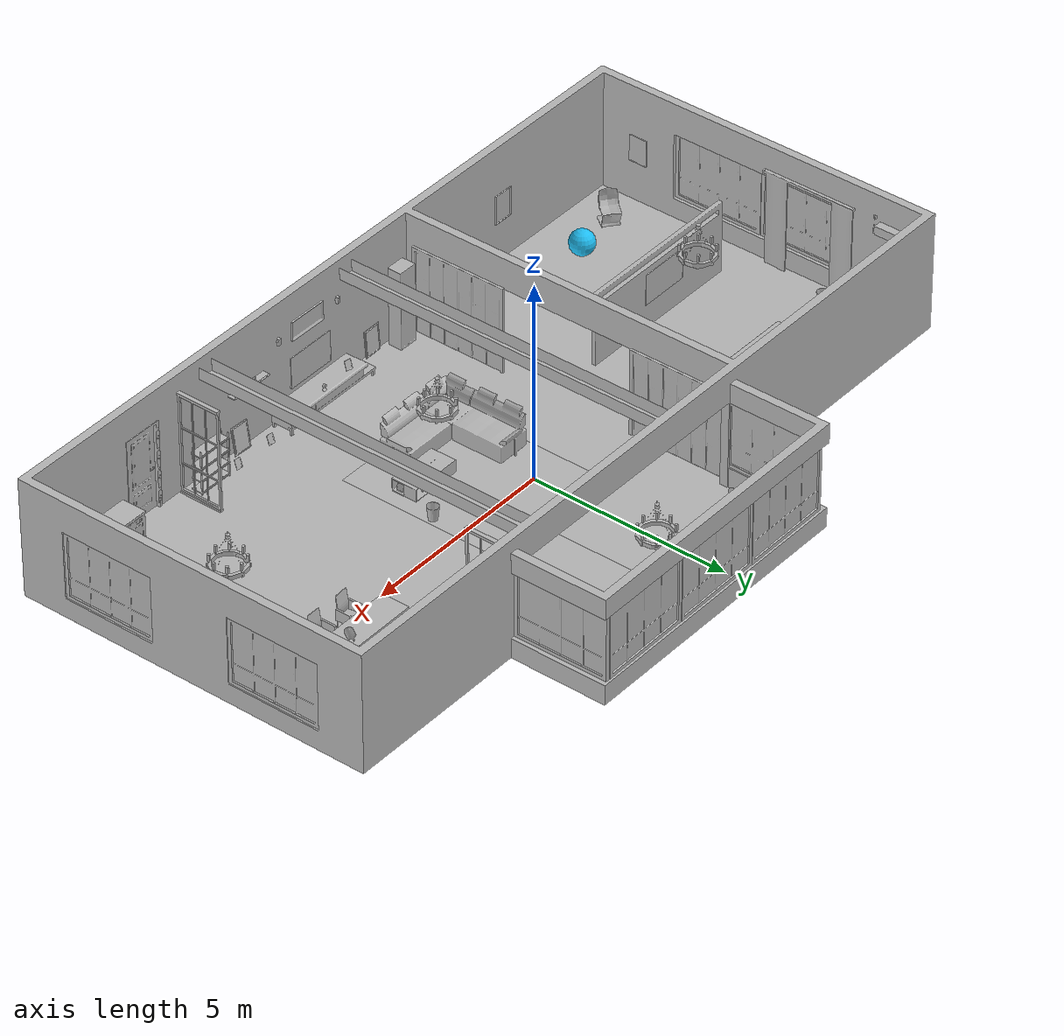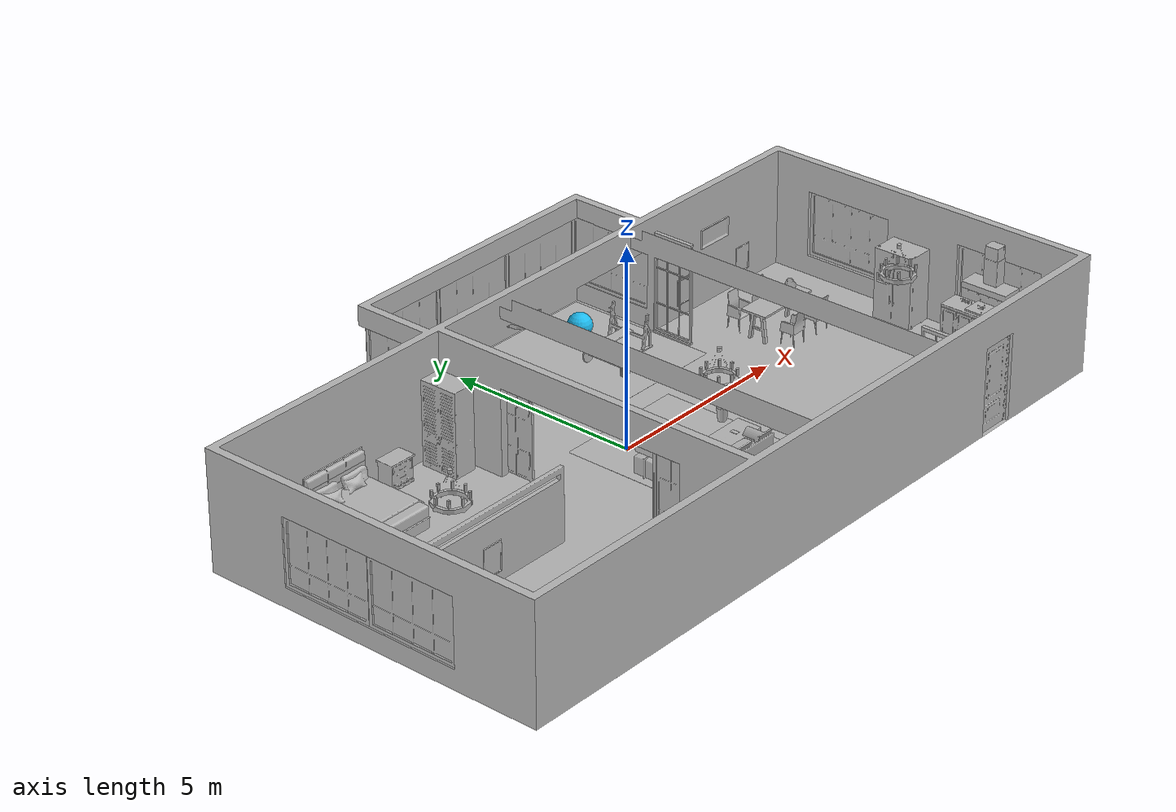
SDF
<?xml version='1.0' encoding='UTF-8'?>
<sdf version="1.6">
    <world name="default">

        <!-- override the default position of the camera !-->
        <gui>
            <camera name="gzclient_camera">
                <pose>0.679719 -0.230569 22.016933 0.000403 1.569797 1.568392</pose>
            </camera>
        </gui>

        <gravity>0 0 -9.8</gravity>
        <magnetic_field>6e-06 2.3e-05 -4.2e-05</magnetic_field>
        <atmosphere type="adiabatic"/>
        <physics name="default_physics" default="0" type="ode">
            <max_step_size>0.001</max_step_size>
            <real_time_factor>1</real_time_factor>
            <real_time_update_rate>1000</real_time_update_rate>
        </physics>
        <scene>
            <ambient>0.4 0.4 0.4 1</ambient>
            <background>0.7 0.7 0.7 1</background>
            <shadows>false</shadows>
            <grid>false</grid>
            <origin_visual>false</origin_visual>
        </scene>
        <spherical_coordinates>
            <surface_model>EARTH_WGS84</surface_model>
            <latitude_deg>0</latitude_deg>
            <longitude_deg>0</longitude_deg>
            <elevation>0</elevation>
            <heading_deg>0</heading_deg>
        </spherical_coordinates>

        <model name="AirconditionerA_01_001">
            <static>true</static>
            <include>
                <uri>model://aws_robomaker_residential_AirconditionerA_01</uri>
            </include>
            <pose frame="">-9.199410 2.411230 2.084544 0 -0 0</pose>
        </model>

        <model name="AirconditionerB_01_001">
            <static>true</static>
            <include>
                <uri>model://aws_robomaker_residential_AirconditionerB_01</uri>
            </include>
            <pose frame="">-2.004656 -5.226610 0.003485 0 -0 0</pose>
        </model>
        <model name="Ball_01_001">
            <static>true</static>
            <include>
                <uri>model://aws_robomaker_residential_Ball_01</uri>
            </include>
            <pose frame="">3.295503 4.225674 0.318684 0 -0 0</pose>
        </model>

        <!-- quick test ball for turtlebot3 -->

        <!-- bedroom ball -->
        <model name="Ball_01_003">
            <static>true</static>
            <include>
                <uri>model://aws_robomaker_residential_Ball_01</uri>
            </include>
            <pose frame="">-6.945503 -4.22174 0.318684 0 -0 0</pose>
        </model>
        <model name="Bed_01_001">
            <static>true</static>
            <include>
                <uri>model://aws_robomaker_residential_Bed_01</uri>
            </include>
            <pose frame="">-6.165067 2.030560 -0.000010 0 -0 0</pose>
        </model>
        <model name="NightStand_01_001">
            <static>true</static>
            <include>
                <uri>model://aws_robomaker_residential_NightStand_01</uri>
            </include>
            <pose frame="">-7.725510 2.860420 0.005258 -0.000002 0 0</pose>
        </model>
        <model name="NightStand_01_002">
            <static>true</static>
            <include>
                <uri>model://aws_robomaker_residential_NightStand_01</uri>
            </include>
            <pose frame="">-4.407341 2.860420 0.005256 0 0.000002 0</pose>
        </model>
        <model name="Board_01_001">
            <static>true</static>
            <include>
                <uri>model://aws_robomaker_residential_Board_01</uri>
            </include>
            <pose frame="">2.779073 -5.392703 1.538173 0 -0 0</pose>
        </model>

        <model name="ChairA_01_001">
            <static>true</static>
            <include>
                <uri>model://aws_robomaker_residential_ChairA_01</uri>
            </include>
            <pose frame="">7.11516 0.209028 0.024685 1e-06 -0 -1.55607</pose>
        </model>
        <model name="ChairA_01_002">
            <static>true</static>
            <include>
                <uri>model://aws_robomaker_residential_ChairA_01</uri>
            </include>
            <pose frame="">6.25506 0.219468 0.011308 0 0 -1.50414</pose>
        </model>
        <model name="ChairA_01_003">
            <static>true</static>
            <include>
                <uri>model://aws_robomaker_residential_ChairA_01</uri>
            </include>
            <pose frame="">6.06678 1.68075 0.01 0 -0 1.56986</pose>
        </model>
        <model name="ChairA_01_004">
            <static>true</static>
            <include>
                <uri>model://aws_robomaker_residential_ChairA_01</uri>
            </include>
            <pose frame="">7.00277 1.67074 0 0 -0 1.52363</pose>
        </model>
        <model name="ChairA_01_005">
            <static>true</static>
            <include>
                <uri>model://aws_robomaker_residential_ChairA_01</uri>
            </include>
            <pose frame="">-8.270940 1.916650 0.036650 0 -0 0</pose>
        </model>
        <model name="ChairD_01_001">
            <static>true</static>
            <include>
                <uri>model://aws_robomaker_residential_ChairD_01</uri>
            </include>
            <pose frame="">-1.380775 4.104456 0 0 -0 0</pose>
        </model>
        <model name="ChairD_01_002">
            <static>true</static>
            <include>
                <uri>model://aws_robomaker_residential_ChairD_01</uri>
            </include>
            <pose frame="">0.325214 4.104456 0 0 -0 -3.138741</pose>
        </model>
        <model name="ChairD_01_003">
            <static>true</static>
            <include>
                <uri>model://aws_robomaker_residential_ChairD_01</uri>
            </include>
            <pose frame="">-8.270775 -4.504456 0 0 -0 0.869673</pose>
        </model>
        <model name="Chandelier_01_001">
            <static>true</static>
            <include>
                <uri>model://aws_robomaker_residential_Chandelier_01</uri>
            </include>
            <pose frame="">1.221061 4.155740 1.295000 0 -0 0</pose>
        </model>
        <model name="Chandelier_01_002">
            <static>true</static>
            <include>
                <uri>model://aws_robomaker_residential_Chandelier_01</uri>
            </include>
            <pose frame="">-6.451061 -0.692040 1.810000 0 -0 0</pose>
        </model>
        <model name="Chandelier_01_003">
            <static>true</static>
            <include>
                <uri>model://aws_robomaker_residential_Chandelier_01</uri>
            </include>
            <pose frame="">7.824061 -1.59 1.7510000 0 -0 0</pose>
        </model>
        <model name="Chandelier_01_004">
            <static>true</static>
            <include>
                <uri>model://aws_robomaker_residential_Chandelier_01</uri>
            </include>
            <pose frame="">1.221061 -1.592040 1.7873000 0 -0 0</pose>
        </model>
        <model name="Carpet_01_001">
            <static>true</static>
            <include>
                <uri>model://aws_robomaker_residential_Carpet_01</uri>
            </include>
            <pose frame="">0.785050 -1.106647 0.001106 0 -0 0</pose>
        </model>
        <model name="Carpet_01_002">
            <static>true</static>
            <include>
                <uri>model://aws_robomaker_residential_Carpet_01</uri>
            </include>
            <pose frame="">2.854050 3.45 0.000585 0 -0 0</pose>
        </model>
        <model name="SecurityCamera_01_001">
            <static>true</static>
            <include>
                <uri>model://aws_robomaker_residential_SecurityCamera_01</uri>
            </include>
            <pose frame="">0.842134 -4.996294 0.495067 0 -0 -2.841039</pose>
        </model>
        <model name="CoffeeTable_01_001">
            <static>true</static>
            <include>
                <uri>model://aws_robomaker_residential_CoffeeTable_01</uri>
            </include>
            <pose frame="">1.512301 -1.733438 0.041983 0.000000 0.000000 0.01000</pose>
        </model>
        <model name="CookingBench_01_001">
            <include>
                <uri>model://aws_robomaker_residential_CookingBench_01</uri>
            </include>
            <pose frame="">9.038383 -3.351140 0.903610 0 -0 3.137133</pose>
            <static> true </static>
        </model>

        <model name="Curtain_01_001">
            <static>true</static>
            <include>
                <uri>model://aws_robomaker_residential_Curtain_01</uri>
            </include>
            <pose frame="">-9.172642 0.203760 0 0 -0 0</pose>
        </model>

        <model name="KitchenTable_01_001">
            <static>true</static>
            <include>
                <uri>model://aws_robomaker_residential_KitchenTable_01</uri>
            </include>
            <pose frame="">6.55269 0.951173 -0.000006 0 -0 -1.564130</pose>
        </model>
        <model name="ReadingDesk_01_001">
            <static>true</static>
            <include>
                <uri>model://aws_robomaker_residential_ReadingDesk_01</uri>
            </include>
            <pose frame="">-8.987262 2.057058 0 0 -0 -0.004638</pose>
        </model>
        <model name="BalconyTable_01_001">
            <static>true</static>
            <include>
                <uri>model://aws_robomaker_residential_BalconyTable_01</uri>
            </include>
            <pose frame="">-0.556240 4.111241 0 0 -0 0</pose>
        </model>

        <model name="Door_01_001">
            <static>true</static>
            <include>
                <uri>model://aws_robomaker_residential_Door_01</uri>
            </include>
            <pose frame="">6.001449 -5.549002 0 0 -0 0</pose>
        </model>

        <model name="Dumbbell_01_001">
            <static>true</static>
            <include>
                <uri>model://aws_robomaker_residential_Dumbbell_01</uri>
            </include>
            <pose frame="">2.512849 2.717787 0.002183 0 -0 0</pose>
        </model>
        <model name="Tablet_01_001">
            <static>true</static>
            <include>
                <uri>model://aws_robomaker_residential_Tablet_01</uri>
            </include>
            <pose frame="">1.572830 -1.775857 0.401790 -0.020625 -0.000080 -0.006317</pose>
        </model>
        <model name="FitnessEquipment_01_001">
            <static>true</static>
            <include>
                <uri>model://aws_robomaker_residential_FitnessEquipment_01</uri>
            </include>
            <pose frame="">3.484720 3.169104 0.003168 0 -0 0</pose>
        </model>
        <model name="FoldingDoor_01_001">
            <static>true</static>
            <include>
                <uri>model://aws_robomaker_residential_FoldingDoor_01</uri>
            </include>
            <pose frame="">-2.461096 1.844219 0.041881 0 -0 0</pose>
        </model>
        <model name="FoldingDoor_01_002">
            <static>true</static>
            <include>
                <uri>model://aws_robomaker_residential_FoldingDoor_01</uri>
            </include>
            <pose frame="">-2.461096 -4.053320 0.041881 0 -0 0</pose>
        </model>
        <model name="Handle_01_001">
            <static>true</static>
            <include>
                <uri>model://aws_robomaker_residential_Handle_01</uri>
            </include>
            <pose frame="">5.724 -5.523 0.9938 0 -0 -3.1415</pose>
        </model>

        <model name="HouseWallB_01_001">
            <static>true</static>
            <include>
                <uri>model://aws_robomaker_residential_HouseWallB_01</uri>
            </include>
            <pose frame="">0 0 0 0 -0 0</pose>
        </model>

        <model name="FloorB_01_001">
            <static>true</static>
            <include>
                <uri>model://aws_robomaker_residential_FloorB_01</uri>
            </include>
            <pose frame="">0 0 0 0 -0 0</pose>
        </model>

        <model name="FoldingDoor_02_001">
            <static>true</static>
            <include>
                <uri>model://aws_robomaker_residential_FoldingDoor_02</uri>
            </include>
            <pose frame="">4.674231 2.46451 0 0 -0 3.14159</pose>
        </model>

        <model name="FoldingDoor_02_002">
            <static>true</static>
            <include>
                <uri>model://aws_robomaker_residential_FoldingDoor_02</uri>
            </include>
            <pose frame="">4.8912 -4.84968 0 0 -0 0</pose>
        </model>

        <model name="KitchenCabinet_01_001">
            <static>true</static>
            <include>
                <uri>model://aws_robomaker_residential_KitchenCabinet_01</uri>
            </include>
            <pose frame="">8.002009 -3.836509 0.012068 0 -0 -3.140001</pose>
        </model>
        <model name="KitchenUtensils_01_001">
            <static>true</static>
            <include>
                <uri>model://aws_robomaker_residential_KitchenUtensils_01</uri>
            </include>
            <pose frame="">9.285478 -5.021261 1.141805 0 -0 0</pose>
        </model>

        <model name="LightC_01_001">
            <static>true</static>
            <include>
                <uri>model://aws_robomaker_residential_LightC_01</uri>
            </include>
            <pose frame="">1.769567 -5.4443710 2.000000 0 -0 0</pose>
        </model>
        <model name="LightC_01_002">
            <static>true</static>
            <include>
                <uri>model://aws_robomaker_residential_LightC_01</uri>
            </include>
            <pose frame="">-0.138245 -5.4443710 2.000000 0 -0 0</pose>
        </model>

        <!-- WALL -->
        <model name="PortraitA_01">
            <static>true</static>
            <include>
                <uri>model://aws_robomaker_residential_PortraitA_01</uri>
            </include>
            <pose frame="">-2.712360 -4.817539 1.00000 0 -0 1.566796</pose>
        </model>

        <model name="PortraitB_01">
            <static>true</static>
            <include>
                <uri>model://aws_robomaker_residential_PortraitB_01</uri>
            </include>
            <pose frame="">-1.279683 -5.429630 0.0 -0.076901 0 -3.116718</pose>
        </model>

        <model name="PortraitB_02">
            <static>true</static>
            <include>
                <uri>model://aws_robomaker_residential_PortraitB_02</uri>
            </include>
            <pose frame="">5.737017 3.080310 0.300000 0 -0 0</pose>
        </model>

        <model name="PortraitB_03">
            <static>true</static>
            <include>
                <uri>model://aws_robomaker_residential_PortraitB_03</uri>
            </include>
            <pose frame="">3.071380 -5.349366 0.005494 -0.168428 0.0 3.104232</pose>
        </model>

        <model name="PortraitA_02">
            <static>true</static>
            <include>
                <uri>model://aws_robomaker_residential_PortraitA_02</uri>
            </include>
            <pose frame="">7.937017 3.080310 0.300000 0 -0 3.14</pose>
        </model>

        <model name="PortraitC_01">
            <static>true</static>
            <include>
                <uri>model://aws_robomaker_residential_PortraitC_01</uri>
            </include>
            <pose frame="">-9.294904 -4.526084 1.000000 0 -0 1.554734</pose>
        </model>

        <model name="PortraitD_01">
            <static>true</static>
            <include>
                <uri>model://aws_robomaker_residential_PortraitD_01</uri>
            </include>
            <pose frame="">0.789763 -5.478725 1.800000 0 -0 3.138531</pose>
        </model>
        <model name="PortraitD_02">
            <static>true</static>
            <include>
                <uri>model://aws_robomaker_residential_PortraitD_02</uri>
            </include>
            <pose frame="">6.870181 3.080310 1.488439 0 -0 0</pose>
        </model>

        <model name="PortraitE_01">
            <static>true</static>
            <include>
                <uri>model://aws_robomaker_residential_PortraitE_01</uri>
            </include>
            <pose frame="">-5.773094 -5.492466 1.000000 0 -0 3.132627</pose>
        </model>
        <model name="PortraitE_02">
            <static>true</static>
            <include>
                <uri>model://aws_robomaker_residential_PortraitE_02</uri>
            </include>
            <pose frame="">-6.193025 -1.590208 0.3 0 -0 0.004290</pose>
        </model>

        <!-- DESK -->
        <model name="DeskPortraitA_01">
            <static>true</static>
            <include>
                <uri>model://aws_robomaker_residential_DeskPortraitA_01</uri>
            </include>
            <pose frame="">-0.036864 -5.110156 0.498660 0 -0 2.927784</pose>
        </model>
        <model name="DeskPortraitA_02">
            <static>true</static>
            <include>
                <uri>model://aws_robomaker_residential_DeskPortraitA_02</uri>
            </include>

            <pose frame="">2.046082 -1.892926 0.0703880 -0.018328 -0.000441 1.576216</pose>
        </model>
        <model name="DeskPortraitC_01">
            <static>true</static>
            <include>
                <uri>model://aws_robomaker_residential_DeskPortraitC_01</uri>
            </include>
            <pose frame="">-7.746377 2.731075 0.694620 0.000488 -0.000359 -0.055499</pose>
        </model>
        <model name="DeskPortraitC_02">
            <static>true</static>
            <include>
                <uri>model://aws_robomaker_residential_DeskPortraitC_02</uri>
            </include>
            <pose frame="">0.964613 -1.586951 0.127676 0.001614 -0.000545 -1.578699</pose>
        </model>
        <model name="DeskPortraitD_01">
            <static>true</static>
            <include>
                <uri>model://aws_robomaker_residential_DeskPortraitD_01</uri>
            </include>
            <pose frame="">2.645560 -5.376225 1.573738 0 -0 -3.112826</pose>
        </model>
        <model name="DeskPortraitD_02">
            <static>true</static>
            <include>
                <uri>model://aws_robomaker_residential_DeskPortraitD_02</uri>
            </include>
            <pose frame="">-0.589211 -5.109890 0.192145 -0.000015 -0.000174 -3.112544</pose>
        </model>
        <model name="DeskPortraitD_03">
            <static>true</static>
            <include>
                <uri>model://aws_robomaker_residential_DeskPortraitD_03</uri>
            </include>
            <pose frame="">1.826729 -1.464881 0.126208 0.000010 0.000006 -3.114380</pose>
        </model>
        <model name="DeskPortraitD_04">
            <static>true</static>
            <include>
                <uri>model://aws_robomaker_residential_DeskPortraitD_04</uri>
            </include>
            <pose frame="">4.302132 -5.176568 0.202496 0.007118 -0.000001 3.046683</pose>
        </model>
        <model name="DeskPortraitB_01">
            <static>true</static>
            <include>
                <uri>model://aws_robomaker_residential_DeskPortraitB_01</uri>
            </include>
            <pose frame="">3.547376 -5.083898 -0.012660 -0.336622 -0.000001 3.046741</pose>
        </model>
        <model name="DeskPortraitB_02">
            <static>true</static>
            <include>
                <uri>model://aws_robomaker_residential_DeskPortraitB_02</uri>
            </include>
            <pose frame="">2.486270 -5.102525 -0.012660 -0.336621 0.000000 3.046798</pose>
        </model>
        <!-- Wall & Desk Portraits END -->

        <model name="Rangehood_01_001">
            <static>true</static>
            <include>
                <uri>model://aws_robomaker_residential_Rangehood_01</uri>
            </include>
            <pose frame="">9.019794 -3.369940 1.507605 0 -0 0</pose>
        </model>

        <model name="Refrigerator_01_001">
            <static>true</static>
            <include>
                <uri>model://aws_robomaker_residential_Refrigerator_01</uri>
            </include>
            <pose frame="">8.702731 -1.032031 0 0 -0 -1.563499</pose>
        </model>
        <model name="SeasoningBox_01_001">
            <static>true</static>
            <include>
                <uri>model://aws_robomaker_residential_SeasoningBox_01</uri>
            </include>
            <pose frame="">9.107968 -2.651726 0.902458 -0.000006 0.000034 0.001290</pose>
        </model>
        <model name="ShoeRack_01_001">
            <static>true</static>
            <include>
                <uri>model://aws_robomaker_residential_ShoeRack_01</uri>
            </include>
            <pose frame="">4.297978 -5.173566 0 0 -0 0</pose>
        </model>
        <model name="SofaC_01_001">
            <static>true</static>
            <include>
                <uri>model://aws_robomaker_residential_SofaC_01</uri>
            </include>
            <pose frame="">0.330699 -1.902792 0.065992 0.000000 0.000000 1.571733</pose>
        </model>
        <model name="Tableware_01_001">
            <static>true</static>
            <include>
                <uri>model://aws_robomaker_residential_Tableware_01</uri>
            </include>
            <pose frame="">7.15317 0.982767 0.817812 -0.001238 -0.000976 1.02476</pose>
        </model>
        <model name="Trash_01_001">
            <static>true</static>
            <include>
                <uri>model://aws_robomaker_residential_Trash_01</uri>
            </include>
            <pose frame="">2.360151 -0.796238 0.011 0 -0 0</pose>
        </model>
        <model name="Trash_01_002">
            <static>true</static>
            <include>
                <uri>model://aws_robomaker_residential_Trash_01</uri>
            </include>
            <pose frame="">-8.704151 1.00058 0.011 0 -0 0</pose>
        </model>
        <model name="TV_01_001">
            <static>true</static>
            <include>
                <uri>model://aws_robomaker_residential_TV_01</uri>
            </include>
            <pose frame="">0.824259 -5.382968 0.676282 0 -0 -1.561744</pose>
        </model>
        <model name="TV_02_001">
            <static>true</static>
            <include>
                <uri>model://aws_robomaker_residential_TV_02</uri>
            </include>
            <pose frame="">-6.197322 -1.388739 0.676282 0 -0 -1.561744</pose>
        </model>
        <model name="TVCabinet_01_001">
            <static>true</static>
            <include>
                <uri>model://aws_robomaker_residential_TVCabinet_01</uri>
            </include>
            <pose frame="">0.629509 -5.183576 -0.017049 0 -0 1.5792</pose>
        </model>
        <model name="Vase_01_001">
            <static>true</static>
            <include>
                <uri>model://aws_robomaker_residential_Vase_01</uri>
            </include>
            <pose frame="">3.055663 -5.413080 1.574958 0.000003 0.001700 0.000840</pose>
        </model>`
        <model name="RoomWall_01_001">
            <static>true</static>
            <include>
                <uri>model://aws_robomaker_residential_RoomWall_01</uri>
            </include>
            <pose frame="">-6.097550 -1.496180 0.028124 0 -0 0</pose>
        </model>

        <model name="Wardrobe_01_001">
            <static>true</static>
            <include>
                <uri>model://aws_robomaker_residential_Wardrobe_01</uri>
            </include>
            <pose frame="">-3.146710 2.476204 0.000704 0 -0 -1.569673</pose>
        </model>
        <model name="RoomWindow_01_001">
            <static>true</static>
            <include>
                <uri>model://aws_robomaker_residential_RoomWindow_01</uri>
            </include>
            <pose frame="">-9.418600 -0.026285 0.502739 0 -0 0</pose>
        </model>
        <model name="RoomWindow_01_002">
            <static>true</static>
            <include>
                <uri>model://aws_robomaker_residential_RoomWindow_01</uri>
            </include>
            <pose frame="">-9.418600 -2.374090 0.502739 0 -0 0</pose>
        </model>
        <model name="RoomWindow_01_003">
            <static>true</static>
            <include>
                <uri>model://aws_robomaker_residential_RoomWindow_01</uri>
            </include>
            <pose frame="">9.422616 -3.373981 0.502739 0 -0 -3.136099</pose>
        </model>
        <model name="RoomWindow_01_004">
            <static>true</static>
            <include>
                <uri>model://aws_robomaker_residential_RoomWindow_01</uri>
            </include>
            <pose frame="">9.422558 0.968520 0.496581 0 -0 -3.136099</pose>
        </model>
        <model name="RoomWindow_01_005">
            <static>true</static>
            <include>
                <uri>model://aws_robomaker_residential_RoomWindow_01</uri>
            </include>
            <pose frame="">4.722317 4.470281 0.502739 0 -0 -3.136099</pose>
        </model>
        <model name="RoomWindow_01_006">
            <static>true</static>
            <include>
                <uri>model://aws_robomaker_residential_RoomWindow_01</uri>
            </include>
            <pose frame="">3.488520 5.600688 0.502739 0 -0 -1.566274</pose>
        </model>
        <model name="RoomWindow_01_007">
            <static>true</static>
            <include>
                <uri>model://aws_robomaker_residential_RoomWindow_01</uri>
            </include>
            <pose frame="">1.140949 5.600688 0.502739 0 -0 -1.566274</pose>
        </model>
        <model name="RoomWindow_01_008">
            <static>true</static>
            <include>
                <uri>model://aws_robomaker_residential_RoomWindow_01</uri>
            </include>
            <pose frame="">-1.199340 5.600688 0.502739 0 -0 -1.566274</pose>
        </model>
        <model name="RoomWindow_01_009">
            <static>true</static>
            <include>
                <uri>model://aws_robomaker_residential_RoomWindow_01</uri>
            </include>
            <pose frame="">-2.396624 4.387607 0.502739 0 -0 0</pose>
        </model>

        <!-- Lights !-->
        <light name="LivingRoom_CeilingLight_0" type="point">
            <pose frame="">1.194296 4.155759 2.2 0 -0 0</pose>
            <diffuse>0.5 0.5 0.5 1</diffuse>
            <specular>0.1 0.1 0.1 1</specular>
            <attenuation>
                <range>20</range>
                <constant>0.32</constant>
                <linear>0.01</linear>
                <quadratic>0.03</quadratic>
            </attenuation>
            <cast_shadows>0</cast_shadows>
            <direction>0 0 -1</direction>
        </light>
        <light name="LivingRoom_CeilingLight_1" type="point">
            <pose frame="">1.194296 -1.589959 2.2 0 -0 0</pose>
            <diffuse>0.5 0.5 0.5 1</diffuse>
            <specular>0.1 0.1 0.1 1</specular>
            <attenuation>
                <range>20</range>
                <constant>0.05</constant>
                <linear>0.01</linear>
                <quadratic>0.09</quadratic>
            </attenuation>
            <cast_shadows>0</cast_shadows>
            <direction>0 0 -1</direction>
        </light>
        <light name="LivingRoom_WallLight_0" type="point">
            <pose frame="">1.76956 -5.444370 2.2 0 -0 0</pose>
            <diffuse>0.24 0.24 0.24 1</diffuse>
            <specular>0.1 0.1 0.1 1</specular>
            <attenuation>
                <range>20</range>
                <constant>0.12</constant>
                <linear>0.00</linear>
                <quadratic>0.03</quadratic>
            </attenuation>
            <cast_shadows>1</cast_shadows>
            <direction>0 0 -1</direction>
        </light>
        <light name="LivingRoom_WallLight_1" type="point">
            <pose frame="">-0.13826 -5.444370 2.2 0 -0 0</pose>
            <diffuse>0.24 0.24 0.24 1</diffuse>
            <specular>0.1 0.1 0.1 1</specular>
            <attenuation>
                <range>20</range>
                <constant>0.12</constant>
                <linear>0.00</linear>
                <quadratic>0.03</quadratic>
            </attenuation>
            <cast_shadows>1</cast_shadows>
            <direction>0 0 -1</direction>
        </light>
        <light name="TV_Light_0" type="point">
            <pose frame="">0.8269 -4.939577 1.1 0 -0 0</pose>
            <diffuse>0.31372 0.31372 0.34901 1</diffuse>
            <specular>0.1 0.1 0.1 1</specular>
            <attenuation>
                <range>3</range>
                <constant>0.10</constant>
                <linear>0.04</linear>
                <quadratic>0.50</quadratic>
            </attenuation>
            <cast_shadows>1</cast_shadows>
            <direction>0 0 -1</direction>
        </light>
        <light name="BedRoom_Portrait_Light_0" type="spot">
            <pose frame="">-6.190379 -1.829697 1.5587 0.3 -0 0.0</pose>
            <diffuse>0.5 0.5 0.5 1</diffuse>
            <specular>0.1 0.1 0.1 1</specular>
            <attenuation>
                <range>20</range>
                <constant>0.50</constant>
                <linear>0.01</linear>
                <quadratic>0.00</quadratic>
            </attenuation>
            <spot>
                <inner_angle>0.6</inner_angle>
                <outer_angle>1.0</outer_angle>
                <falloff>1.0</falloff>
            </spot>
            <cast_shadows>1</cast_shadows>
            <direction>0 0 -1</direction>
        </light>
        <light name="BedRoom_CeilingLight_0" type="point">
            <pose frame="">-6.451061 -0.692040 2.000000 0 -0 0</pose>
            <diffuse>0.5 0.5 0.5 1</diffuse>
            <specular>0.1 0.1 0.1 1</specular>
            <attenuation>
                <range>20</range>
                <constant>0.32</constant>
                <linear>0.01</linear>
                <quadratic>0.03</quadratic>
            </attenuation>
            <cast_shadows>0</cast_shadows>
            <direction>0 0 -1</direction>
        </light>
        <light name="Kitchen_CeilingLight_0" type="point">
            <pose frame="">7.8582 -1.5905 2.280000 0 -0 0</pose>
            <diffuse>0.5 0.5 0.5 1</diffuse>
            <specular>0.1 0.1 0.1 1</specular>
            <attenuation>
                <range>20</range>
                <constant>0.3</constant>
                <linear>0.01</linear>
                <quadratic>0.01</quadratic>
            </attenuation>
            <cast_shadows>0</cast_shadows>
            <direction>0 0 -1</direction>
        </light>
    </world>
</sdf>

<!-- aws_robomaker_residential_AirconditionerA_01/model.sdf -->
<sdf version="1.6">
  <model name="aws_robomaker_residential_AirconditionerA_01">
    <link name="link">
      <inertial>
        <mass>1</mass>
      </inertial>
      <collision name="collision">
        <geometry>
          <mesh>
            <uri>model://aws_robomaker_residential_AirconditionerA_01/meshes/aws_AirconditionerA_01_collision.DAE</uri>
            <scale>1 1 1</scale>
          </mesh>
        </geometry>
      </collision>
      <visual name="visual">
	    <geometry>
          <mesh>
            <uri>model://aws_robomaker_residential_AirconditionerA_01/meshes/aws_AirconditionerA_01_visual.DAE</uri>
          </mesh>
        </geometry>
      <meta> <layer> 1 </layer></meta>
</visual>
    </link>
	<static>1</static>
  </model>
</sdf>

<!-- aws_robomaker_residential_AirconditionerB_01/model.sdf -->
<sdf version="1.6">
  <model name="aws_robomaker_residential_AirconditionerB_01">
    <link name="link">
      <inertial>
        <mass>1</mass>
      </inertial>
      <collision name="collision">
        <geometry>
          <mesh>
            <uri>model://aws_robomaker_residential_AirconditionerB_01/meshes/aws_AirconditionerB_01_collision.DAE</uri>
            <scale>1 1 1</scale>
          </mesh>
        </geometry>
      </collision>
      <visual name="visual">
	    <geometry>
          <mesh>
            <uri>model://aws_robomaker_residential_AirconditionerB_01/meshes/aws_AirconditionerB_01_visual.DAE</uri>
          </mesh>
        </geometry>
      <meta> <layer> 1 </layer></meta>
</visual>
    </link>
  </model>
</sdf>

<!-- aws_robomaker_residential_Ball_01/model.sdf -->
<sdf version="1.6">
  <model name="aws_robomaker_residential_Ball_01">
    <link name="link">
      <inertial>
        <mass>0.12</mass>
        <!-- 2r = 62cm -->
          <inertia>
            <ixx>0.030752</ixx>
            <ixy>0</ixy>
            <ixz>0</ixz>
            <iyy>0.030752</iyy>
            <iyz>0</iyz>
            <izz>0.030752</izz>
          </inertia>
      </inertial>
      <collision name="collision">

        <geometry>
          <sphere>
            <radius>0.31 </radius>
          </sphere>

        </geometry>

        <surface>
          <friction>
            <ode>
              <mu>0.85</mu>
              <mu2>0.85</mu2>
            </ode>
          </friction>

        <!-- Add some bounciness to the ball -->
          <contact>
            <ode>
              <kd>8500</kd>
              <max_vel>5.1</max_vel>
            </ode>
          </contact>
        </surface>

      </collision>
      <visual name="visual">
	    <geometry>
          <sphere>
            <radius>0.31 </radius>
          </sphere>
      </geometry>
          <material>
            <diffuse>0.12 0.76 0.97 1</diffuse>
            <ambient>0.03 0.21 0.27 1</ambient>
          </material>
      <meta> <layer> 1 </layer></meta>
</visual>
    </link>
  </model>
</sdf>

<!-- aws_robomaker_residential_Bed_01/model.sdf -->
<sdf version="1.6">
  <model name="aws_robomaker_residential_Bed_01">
    <link name="link">
      <inertial>
        <mass>22.6</mass>
      </inertial>
      <collision name="collision">
        <geometry>
          <mesh>
            <uri>model://aws_robomaker_residential_Bed_01/meshes/aws_Bed_01_collision.DAE</uri>
            <scale>1 1 1</scale>
          </mesh>
        </geometry>
      </collision>
      <visual name="visual">
	    <geometry>
          <mesh>
            <uri>model://aws_robomaker_residential_Bed_01/meshes/aws_Bed_01_visual.DAE</uri>
          </mesh>
        </geometry>
      <meta> <layer> 1 </layer></meta>
</visual>
    </link>
  <static>1</static>
  </model>
</sdf>

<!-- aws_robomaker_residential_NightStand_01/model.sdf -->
<sdf version="1.6">
  <model name="aws_robomaker_residential_NightStand_01">
    <link name="link">
      <inertial>
        <mass>13.6</mass>

        <inertia>
          <ixx>0.6165</ixx>
          <ixy>0</ixy>
          <ixz>0</ixz>
          <iyy>1.29664</iyy>
          <iyz>0</iyz>
          <izz>0.7706</izz>
        </inertia>

      </inertial>
      <collision name="collision">
        <geometry>
          <mesh>
            <uri>model://aws_robomaker_residential_NightStand_01/meshes/aws_NightStand_01_collision.DAE</uri>
            <scale>1 1 1</scale>
          </mesh>
        </geometry>
      </collision>
      <visual name="visual">
	    <geometry>
          <mesh>
            <uri>model://aws_robomaker_residential_NightStand_01/meshes/aws_NightStand_01_visual.DAE</uri>
          </mesh>
        </geometry>
      <meta> <layer> 1 </layer></meta>
</visual>
    </link>
    <static>1</static>
  </model>
</sdf>

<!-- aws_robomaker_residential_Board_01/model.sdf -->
<sdf version="1.6">
  <model name="aws_robomaker_residential_Board_01">
    <link name="link">
      <inertial>
        <mass>1</mass>
      </inertial>
      <collision name="collision">
        <geometry>
          <mesh>
            <uri>model://aws_robomaker_residential_Board_01/meshes/aws_Board_01_collision.DAE</uri>
            <scale>1 1 1</scale>
          </mesh>
        </geometry>
      </collision>
      <visual name="visual">
	    <geometry>
          <mesh>
            <uri>model://aws_robomaker_residential_Board_01/meshes/aws_Board_01_visual.DAE</uri>
          </mesh>
        </geometry>
      <meta> <layer> 2 </layer></meta>
</visual>
    </link>

    <static>1</static>
  </model>
</sdf>

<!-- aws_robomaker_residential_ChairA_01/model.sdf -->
<sdf version="1.6">
  <model name="aws_robomaker_residential_ChairA_01">
    <link name="link">
      <inertial>
          <mass>7.5</mass>
          <inertia>
            <ixy>0</ixy>
            <ixz>0</ixz>
            <iyz>0</iyz>
            <ixx>0.217</ixx>
            <iyy>0.217</iyy>
            <izz>0.067</izz>
          </inertia>
      </inertial>

      <collision name="collision">
        <geometry>
          <mesh>
            <uri>model://aws_robomaker_residential_ChairA_01/meshes/aws_ChairA_01_collision.DAE</uri>
            <scale>1 1 1</scale>
          </mesh>
        </geometry>
      </collision>
      <visual name="visual">
	    <geometry>
          <mesh>
            <uri>model://aws_robomaker_residential_ChairA_01/meshes/aws_ChairA_01_visual.DAE</uri>
          </mesh>
        </geometry>
      <meta> <layer> 1 </layer></meta>
</visual>
    </link>
  </model>
</sdf>

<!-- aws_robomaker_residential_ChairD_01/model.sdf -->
<sdf version="1.6">
  <model name="aws_robomaker_residential_ChairD_01">
    <link name="link">

      <inertial>
        <mass>4.5</mass>
          <inertia>
            <ixy>0</ixy>
            <ixz>0</ixz>
            <iyz>0</iyz>
            <ixx>0.217</ixx>
            <iyy>0.217</iyy>
            <izz>0.067</izz>
          </inertia>
      </inertial>

      <collision name="collision">

        <geometry>
          <mesh>
            <uri>model://aws_robomaker_residential_ChairD_01/meshes/aws_ChairD_01_collision.DAE</uri>
            <scale>1 1 1</scale>
          </mesh>
        </geometry>

      </collision>
      <visual name="visual">
	    <geometry>
          <mesh>
            <uri>model://aws_robomaker_residential_ChairD_01/meshes/aws_ChairD_01_visual.DAE</uri>
          </mesh>
        </geometry>
      <meta> <layer> 1 </layer></meta>
</visual>
    </link>
  </model>
</sdf>

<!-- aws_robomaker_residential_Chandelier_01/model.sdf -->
<sdf version="1.6">
  <model name="aws_robomaker_residential_Chandelier_01">
    <link name="link">
      <inertial>
        <mass>1</mass>
      </inertial>
      <collision name="collision">
        <geometry>
          <mesh>
            <uri>model://aws_robomaker_residential_Chandelier_01/meshes/aws_Chandelier_01_collision.DAE</uri>
            <scale>1 1 1</scale>
          </mesh>
        </geometry>
      </collision>
      <visual name="visual">
	    <geometry>
          <mesh>
            <uri>model://aws_robomaker_residential_Chandelier_01/meshes/aws_Chandelier_01_visual.DAE</uri>
          </mesh>
        </geometry>
      <meta> <layer> 2 </layer></meta>
</visual>
    </link>
	<static>1</static>
  </model>
</sdf>

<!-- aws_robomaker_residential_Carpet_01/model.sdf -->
<sdf version="1.6">
  <model name="aws_robomaker_residential_Carpet_01">
    <link name="link">
      <inertial>
        <mass>8.1</mass>
      </inertial>

      <collision name="collision">

        <geometry>
          <mesh>
            <uri>model://aws_robomaker_residential_Carpet_01/meshes/aws_Carpet_01_collision.DAE</uri>
            <scale>1 1 0.95</scale>
          </mesh>
        </geometry>

        <surface>
          <friction>
            <ode>
              <mu>100</mu>
              <mu2>50</mu2>
            </ode>
          </friction>
          <contact>
            <ode>
            </ode>
          </contact>
        </surface>

        <pose>0 0 -0.01 0 0 0 </pose>
      </collision>

      <visual name="visual">
	    <geometry>
          <mesh>
            <uri>model://aws_robomaker_residential_Carpet_01/meshes/aws_Carpet_01_visual.DAE</uri>
          </mesh>
        </geometry>
      <meta> <layer> 1 </layer></meta>
</visual>
    </link>

    <static>1</static>

  </model>
</sdf>

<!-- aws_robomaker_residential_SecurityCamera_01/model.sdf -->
<sdf version="1.6">
  <model name="aws_robomaker_residential_SecurityCamera_01">
    <link name="link">
      <inertial>
        <mass>1</mass>
        <inertia>
          <ixx>18.2222</ixx>
          <ixy>0</ixy>
          <ixz>0</ixz>
          <iyy>18.2222</iyy>
          <iyz>0</iyz>
          <izz>0.0018767</izz>
        </inertia>
      </inertial>
      <collision name="collision">
        <geometry>
          <mesh>
            <uri>model://aws_robomaker_residential_SecurityCamera_01/meshes/aws_SecurityCamera_01_collision.DAE</uri>
            <scale>1 1 1</scale>
          </mesh>
        </geometry>
      </collision>
      <visual name="visual">
	    <geometry>
          <mesh>
            <uri>model://aws_robomaker_residential_SecurityCamera_01/meshes/aws_SecurityCamera_01_visual.DAE</uri>
          </mesh>
        </geometry>
        <meta>
          <layer>2</layer>
        </meta>
      </visual>
    </link>
  </model>
</sdf>

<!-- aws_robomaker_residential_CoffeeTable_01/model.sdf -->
<sdf version="1.6">
  <model name="aws_robomaker_residential_CoffeeTable_01">
    <link name="link">
      <inertial>
        <mass>21.7</mass>

        <inertia>
          <ixx>0.8137499999999998</ixx>
          <ixy>0</ixy>
          <ixz>0</ixz>
          <iyy>2.76675</iyy>
          <iyz>0</iyz>
          <izz>3.254</izz>
        </inertia>

      </inertial>

      <collision name="collision">
        <geometry>
          <mesh>
            <uri>model://aws_robomaker_residential_CoffeeTable_01/meshes/aws_CoffeeTable_01_collision.DAE</uri>
            <scale>1 1 1</scale>
          </mesh>
        </geometry>

        <surface>
          <contact>
            <ode>
              <max_vel>0.01</max_vel>
            </ode>
          </contact>
         </surface>
      </collision>

      <visual name="visual">
	    <geometry>
          <mesh>
            <uri>model://aws_robomaker_residential_CoffeeTable_01/meshes/aws_CoffeeTable_01_visual.DAE</uri>
          </mesh>
        </geometry>
      <meta> <layer> 1 </layer></meta>
</visual>
    </link>
    <static>1</static>
  </model>
</sdf>

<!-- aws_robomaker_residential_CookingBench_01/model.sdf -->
<sdf version="1.6">
  <model name="aws_robomaker_residential_CookingBench_01">
    <link name="link">
      <inertial>
        <mass>1</mass>
      </inertial>
      <collision name="collision">
        <geometry>
          <mesh>
            <uri>model://aws_robomaker_residential_CookingBench_01/meshes/aws_CookingBench_01_collision.DAE</uri>
            <scale>1 1 1</scale>
          </mesh>
        </geometry>
      </collision>
      <visual name="visual">
	    <geometry>
          <mesh>
            <uri>model://aws_robomaker_residential_CookingBench_01/meshes/aws_CookingBench_01_visual.DAE</uri>
          </mesh>
        </geometry>
      <meta> <layer> 1 </layer></meta>
</visual>
    </link>
  </model>
</sdf>

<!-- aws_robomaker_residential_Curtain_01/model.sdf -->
<sdf version="1.6">
  <model name="aws_robomaker_residential_Curtain_01">
    <link name="link">
      <inertial>
        <mass>1</mass>
      </inertial>
      <collision name="collision">
        <geometry>
          <mesh>
            <uri>model://aws_robomaker_residential_Curtain_01/meshes/aws_Curtain_01_collision.DAE</uri>
            <scale>1 1 1</scale>
          </mesh>
        </geometry>
      </collision>
      <visual name="visual">
	    <geometry>
          <mesh>
            <uri>model://aws_robomaker_residential_Curtain_01/meshes/aws_Curtain_01_visual.DAE</uri>
          </mesh>
        </geometry>
      <meta> <layer> 2 </layer></meta>
</visual>
    </link>
	<static>1</static>
  </model>
</sdf>

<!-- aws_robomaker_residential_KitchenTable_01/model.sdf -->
<sdf version="1.6">
  <model name="aws_robomaker_residential_KitchenTable_01">
    <link name="link">
      <inertial>
        <mass>12.3</mass>
      </inertial>
      <collision name="collision">
        <geometry>
          <mesh>
            <uri>model://aws_robomaker_residential_KitchenTable_01/meshes/aws_KitchenTable_01_collision.DAE</uri>
            <scale>1 1 1</scale>
          </mesh>
        </geometry>
      </collision>
      <visual name="visual">
	    <geometry>
          <mesh>
            <uri>model://aws_robomaker_residential_KitchenTable_01/meshes/aws_KitchenTable_01_visual.DAE</uri>
          </mesh>
        </geometry>
      <meta> <layer> 1 </layer></meta>
</visual>
    </link>
  </model>
</sdf>

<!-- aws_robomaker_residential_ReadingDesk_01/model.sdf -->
<sdf version="1.6">
  <model name="aws_robomaker_residential_ReadingDesk_01">
    <link name="link">
      <inertial>
        <mass>14.6</mass>
          <inertia>
            <ixx>0.78</ixx>
            <ixy>0</ixy>
            <ixz>0</ixz>
            <iyy>0.273</iyy>
            <iyz>0</iyz>
            <izz> 0.57375</izz>
          </inertia>
      </inertial>
      <collision name="collision">
        <geometry>
          <mesh>
            <uri>model://aws_robomaker_residential_ReadingDesk_01/meshes/aws_ReadingDesk_01_collision.DAE</uri>
            <scale>1 1 1</scale>
          </mesh>
        </geometry>
      </collision>
      <visual name="visual">
	    <geometry>
          <mesh>
            <uri>model://aws_robomaker_residential_ReadingDesk_01/meshes/aws_ReadingDesk_01_visual.DAE</uri>
          </mesh>
        </geometry>
      <meta> <layer> 1 </layer></meta>
</visual>
    </link>
  </model>
</sdf>

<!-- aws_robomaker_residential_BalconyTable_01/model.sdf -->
<sdf version="1.6">
  <model name="aws_robomaker_residential_BalconyTable_01">
    <link name="link">
      <inertial>
        <mass>15</mass>
      </inertial>
      <collision name="collision">
        <geometry>
          <mesh>
            <uri>model://aws_robomaker_residential_BalconyTable_01/meshes/aws_BalconyTable_01_collision.DAE</uri>
            <scale>1 1 1</scale>
          </mesh>
        </geometry>
      </collision>
      <visual name="visual">
	    <geometry>
          <mesh>
            <uri>model://aws_robomaker_residential_BalconyTable_01/meshes/aws_BalconyTable_01_visual.DAE</uri>
          </mesh>
        </geometry>
      <meta> <layer> 1 </layer></meta>
</visual>
    </link>
  </model>
</sdf>

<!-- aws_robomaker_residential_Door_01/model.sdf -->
<sdf version="1.6">
  <model name="aws_robomaker_residential_Door_01">
    <link name="link">
      <inertial>
        <mass>1</mass>
      </inertial>
      <collision name="collision">
        <geometry>
          <mesh>
            <uri>model://aws_robomaker_residential_Door_01/meshes/aws_Door_01_collision.DAE</uri>
            <scale>1 1 1</scale>
          </mesh>
        </geometry>
      </collision>
      <visual name="visual">
	    <geometry>
          <mesh>
            <uri>model://aws_robomaker_residential_Door_01/meshes/aws_Door_01_visual.DAE</uri>
          </mesh>
        </geometry>
      <meta> <layer> 2 </layer></meta>
</visual>
    </link>
	<static>1</static>
  </model>
</sdf>

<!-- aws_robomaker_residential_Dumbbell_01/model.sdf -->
<sdf version="1.6">
  <model name="aws_robomaker_residential_Dumbbell_01">
    <link name="link">
      <inertial>
        <mass>80</mass>

        <!-- slender rod -->
        <inertia>
          <ixx>14.601</ixx>
          <ixy>0</ixy>
          <ixz>0</ixz>
          <iyy>0</iyy>
          <iyz>0</iyz>
          <izz>14.601</izz>
        </inertia>
      </inertial>
      <collision name="collision">
        <geometry>
          <mesh>
            <uri>model://aws_robomaker_residential_Dumbbell_01/meshes/aws_Dumbbell_01_collision.DAE</uri>
            <scale>1 1 1</scale>
          </mesh>
        </geometry>
        <max_contacts>10</max_contacts>
          <surface>
            <contact>
              <ode/>
            </contact>
            <bounce/>
            <friction>
              <torsional>
                <ode/>
              </torsional>
              <ode/>
            </friction>
          </surface>
      </collision>
      <visual name="visual">
	    <geometry>
          <mesh>
            <uri>model://aws_robomaker_residential_Dumbbell_01/meshes/aws_Dumbbell_01_visual.DAE</uri>
          </mesh>
        </geometry>
      <meta> <layer> 1 </layer></meta>
</visual>
    </link>
    <static>1</static>
  </model>
</sdf>

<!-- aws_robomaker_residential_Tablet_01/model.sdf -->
<sdf version="1.6">
  <model name="aws_robomaker_residential_Tablet_01">
    <link name="link">
      <inertial>
        <mass>0.5</mass>
        <inertia>
          <ixx>0.035652</ixx>
          <ixy>0</ixy>
          <ixz>0</ixz>
          <iyy>0.01</iyy>
          <iyz>0</iyz>
          <izz>0.04120698</izz>
        </inertia>
      </inertial>
      <collision name="collision">
        <geometry>
          <mesh>
            <uri>model://aws_robomaker_residential_Tablet_01/meshes/aws_Tablet_01_collision.DAE</uri>
            <scale>1 1 1</scale>
          </mesh>
        </geometry>
      </collision>
      <visual name="visual">
	    <geometry>
          <mesh>
            <uri>model://aws_robomaker_residential_Tablet_01/meshes/aws_Tablet_01_visual.DAE</uri>
          </mesh>
        </geometry>
        <meta>
          <layer>2</layer>
        </meta>
      </visual>
    </link>
	<static>1</static>
  </model>
</sdf>

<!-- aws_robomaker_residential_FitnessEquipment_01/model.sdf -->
<sdf version="1.6">
  <model name="aws_robomaker_residential_FitnessEquipment_01">
    <link name="link">
      <inertial>
        <mass>80</mass>
      </inertial>
      <collision name="collision">
        <geometry>
          <mesh>
            <uri>model://aws_robomaker_residential_FitnessEquipment_01/meshes/aws_FitnessEquipment_01_collision.DAE</uri>
            <scale>1 1 1</scale>
          </mesh>
        </geometry>
      </collision>
      <visual name="visual">
	    <geometry>
          <mesh>
            <uri>model://aws_robomaker_residential_FitnessEquipment_01/meshes/aws_FitnessEquipment_01_visual.DAE</uri>
          </mesh>
        </geometry>
      <meta> <layer> 1 </layer></meta>
</visual>
    </link>
  <static>1</static>
  </model>
</sdf>

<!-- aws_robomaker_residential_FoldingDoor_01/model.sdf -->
<sdf version="1.6">
  <model name="aws_robomaker_residential_FoldingDoor_01">
    <link name="link">
      <inertial>
        <mass>1</mass>
      </inertial>
      <collision name="collision">
        <geometry>
          <mesh>
            <uri>model://aws_robomaker_residential_FoldingDoor_01/meshes/aws_FoldingDoor_01_collision.DAE</uri>
            <scale>1 1 1</scale>
          </mesh>
        </geometry>
      </collision>
      <visual name="visual">
	    <geometry>
          <mesh>
            <uri>model://aws_robomaker_residential_FoldingDoor_01/meshes/aws_FoldingDoor_01_visual.DAE</uri>
          </mesh>
        </geometry>
      <meta> <layer> 2 </layer></meta>
</visual>
    </link>
	<static>1</static>
  </model>
</sdf>

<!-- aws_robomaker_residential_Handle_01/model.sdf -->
<sdf version="1.6">
  <model name="aws_robomaker_residential_Handle_01">
    <link name="link">
      <inertial>
        <mass>1</mass>
      </inertial>
      <collision name="collision">
        <geometry>
          <mesh>
            <uri>model://aws_robomaker_residential_Handle_01/meshes/aws_Handle_01_collision.DAE</uri>
            <scale>1 1 1</scale>
          </mesh>
        </geometry>
      </collision>
      <visual name="visual">
	    <geometry>
          <mesh>
            <uri>model://aws_robomaker_residential_Handle_01/meshes/aws_Handle_01_visual.DAE</uri>
          </mesh>
        </geometry>
      <meta> <layer> 2 </layer></meta>
</visual>
    </link>
	<static>1</static>
  </model>
</sdf>

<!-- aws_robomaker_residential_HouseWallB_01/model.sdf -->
<sdf version="1.6">
  <model name="aws_robomaker_residential_HouseWallB_01">
    <link name="link">
      <inertial>
        <mass>1</mass>
      </inertial>
      <collision name="collision">
        <geometry>
          <mesh>
            <uri>model://aws_robomaker_residential_HouseWallB_01/meshes/aws_HouseWallB_01_collision.DAE</uri>
            <scale>1 1 1</scale>
          </mesh>
        </geometry>
      </collision>
      <visual name="visual">
	    <geometry>
          <mesh>
            <uri>model://aws_robomaker_residential_HouseWallB_01/meshes/aws_HouseWallB_01_visual.DAE</uri>
          </mesh>
        </geometry>
      <meta> <layer> 2 </layer></meta>
</visual>
    </link>
<static>1</static>
  </model>
</sdf>

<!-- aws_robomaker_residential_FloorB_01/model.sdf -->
<sdf version="1.6">
  <model name="aws_robomaker_residential_FloorB_01">
    <link name="link">
      <inertial>
        <mass>100</mass>
      </inertial>

      <collision name="collision">
        <geometry>
          <mesh>
            <uri>model://aws_robomaker_residential_FloorB_01/meshes/aws_FloorB_01_collision.DAE</uri>
            <scale>1 1 0.9</scale>
          </mesh>
        </geometry>

        <surface>
          <friction>
            <ode>
              <mu>100</mu>
              <mu2>50</mu2>
            </ode>
          </friction>
        </surface>
      </collision>

      <visual name="visual">
	    <geometry>
          <mesh>
            <uri>model://aws_robomaker_residential_FloorB_01/meshes/aws_FloorB_01_visual.DAE</uri>
          </mesh>
        </geometry>
      <meta> <layer> 1 </layer></meta>
</visual>
    </link>

	<static>1</static>
  </model>
</sdf>

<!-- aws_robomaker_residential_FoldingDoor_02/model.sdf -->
<sdf version="1.6">
  <model name="aws_robomaker_residential_FoldingDoor_02">
    <link name="link">
      <inertial>
        <mass>1</mass>
      </inertial>
      <collision name="collision">
        <geometry>
          <mesh>
            <uri>model://aws_robomaker_residential_FoldingDoor_02/meshes/aws_FoldingDoor_02_collision.DAE</uri>
            <scale>1 1 1</scale>
          </mesh>
        </geometry>
      </collision>
      <visual name="visual">
	    <geometry>
          <mesh>
            <uri>model://aws_robomaker_residential_FoldingDoor_02/meshes/aws_FoldingDoor_02_visual.DAE</uri>
          </mesh>
        </geometry>
      <meta> <layer> 2 </layer></meta>
</visual>
    </link>
<static>1</static>
  </model>
</sdf>

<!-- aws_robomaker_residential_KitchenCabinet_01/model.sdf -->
<sdf version="1.6">
  <model name="aws_robomaker_residential_KitchenCabinet_01">
    <link name="link">
      <inertial>
        <mass>1</mass>
      </inertial>
      <collision name="collision">
        <laser_retro>0</laser_retro>
        <max_contacts>10</max_contacts>
        <geometry>
          <mesh>
            <uri>model://aws_robomaker_residential_KitchenCabinet_01/meshes/aws_KitchenCabinet_01_collision.DAE</uri>
            <scale>1 1 1</scale>
          </mesh>
        </geometry>
      </collision>
      <visual name="visual">
	    <geometry>
          <mesh>
            <uri>model://aws_robomaker_residential_KitchenCabinet_01/meshes/aws_KitchenCabinet_01_visual.DAE</uri>
          </mesh>
        </geometry>
      <meta> <layer> 1 </layer></meta>
</visual>
    </link>

    <static>1</static>
  </model>
</sdf>

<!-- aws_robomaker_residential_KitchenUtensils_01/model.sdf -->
<sdf version="1.6">
  <model name="aws_robomaker_residential_KitchenUtensils_01">
    <link name="link">
      <inertial>
        <mass>1</mass>
      </inertial>
      <collision name="collision">
        <geometry>
          <mesh>
            <uri>model://aws_robomaker_residential_KitchenUtensils_01/meshes/aws_KitchenUtensils_01_collision.DAE</uri>
            <scale>1 1 1</scale>
          </mesh>
        </geometry>
      </collision>
      <visual name="visual">
	    <geometry>
          <mesh>
            <uri>model://aws_robomaker_residential_KitchenUtensils_01/meshes/aws_KitchenUtensils_01_visual.DAE</uri>
          </mesh>
        </geometry>
      <meta> <layer> 1 </layer></meta>
</visual>
    </link>
	<static>1</static>
  </model>
</sdf>

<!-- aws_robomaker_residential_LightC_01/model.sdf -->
<sdf version="1.6">
  <model name="aws_robomaker_residential_LightC_01">
    <link name="link">
      <inertial>
        <mass>1</mass>
      </inertial>
      <collision name="collision">
        <geometry>
          <mesh>
            <uri>model://aws_robomaker_residential_LightC_01/meshes/aws_LightC_01_collision.DAE</uri>
            <scale>1 1 1</scale>
          </mesh>
        </geometry>
      </collision>
      <visual name="visual">
	    <geometry>
          <mesh>
            <uri>model://aws_robomaker_residential_LightC_01/meshes/aws_LightC_01_visual.DAE</uri>
          </mesh>
        </geometry>
      <meta> <layer> 2 </layer></meta>
</visual>
    </link>
	<static>1</static>
  </model>
</sdf>

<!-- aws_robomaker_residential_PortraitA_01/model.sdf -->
<sdf version="1.6">
  <model name="aws_robomaker_residential_PortraitA_01">
    <link name="link">
      <inertial>
        <mass>1</mass>
      </inertial>
      <collision name="collision">
        <geometry>
          <mesh>
            <uri>model://aws_robomaker_residential_PortraitA_01/meshes/aws_PortraitA_01_collision.DAE</uri>
            <scale>1 1 1</scale>
          </mesh>
        </geometry>
      </collision>
      <visual name="visual">
	    <geometry>
          <mesh>
            <uri>model://aws_robomaker_residential_PortraitA_01/meshes/aws_PortraitA_01_visual.DAE</uri>
          </mesh>
        </geometry>
      <meta> <layer> 2 </layer></meta>
</visual>
    </link>
	<static>1</static>
  </model>
</sdf>

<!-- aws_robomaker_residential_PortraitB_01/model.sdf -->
<sdf version="1.6">
  <model name="aws_robomaker_residential_PortraitB_01">
    <link name="link">
      <inertial>
        <mass>1</mass>
      </inertial>
      <collision name="collision">
        <geometry>
          <mesh>
            <uri>model://aws_robomaker_residential_PortraitB_01/meshes/aws_PortraitB_01_collision.DAE</uri>
            <scale>1 1 1</scale>
          </mesh>
        </geometry>
      </collision>
      <visual name="visual">
	    <geometry>
          <mesh>
            <uri>model://aws_robomaker_residential_PortraitB_01/meshes/aws_PortraitB_01_visual.DAE</uri>
          </mesh>
        </geometry>
      <meta> <layer> 2 </layer></meta>
</visual>
    </link>
	<static>1</static>
  </model>
</sdf>

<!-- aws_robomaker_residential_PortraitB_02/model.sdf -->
<sdf version="1.6">
  <model name="aws_robomaker_residential_PortraitB_02">
    <link name="link">
      <inertial>
        <mass>1</mass>
      </inertial>
      <collision name="collision">
        <geometry>
          <mesh>
            <uri>model://aws_robomaker_residential_PortraitB_02/meshes/aws_PortraitB_01_collision.DAE</uri>
            <scale>1 1 1</scale>
          </mesh>
        </geometry>
      </collision>
      <visual name="visual">
	    <geometry>
          <mesh>
            <uri>model://aws_robomaker_residential_PortraitB_02/meshes/aws_PortraitB_01_visual.DAE</uri>
          </mesh>
        </geometry>
      <meta> <layer> 2 </layer></meta>
</visual>
    </link>
	<static>1</static>
  </model>
</sdf>

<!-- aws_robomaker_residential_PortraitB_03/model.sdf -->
<sdf version="1.6">
  <model name="aws_robomaker_residential_PortraitB_03">
    <link name="link">
      <inertial>
        <mass>1</mass>
      </inertial>
      <collision name="collision">
        <geometry>
          <mesh>
            <uri>model://aws_robomaker_residential_PortraitB_03/meshes/aws_PortraitB_01_collision.DAE</uri>
            <scale>1 1 1</scale>
          </mesh>
        </geometry>
      </collision>
      <visual name="visual">
	    <geometry>
          <mesh>
            <uri>model://aws_robomaker_residential_PortraitB_03/meshes/aws_PortraitB_01_visual.DAE</uri>
          </mesh>
        </geometry>
      <meta> <layer> 2 </layer></meta>
</visual>
    </link>
	<static>1</static>
  </model>
</sdf>

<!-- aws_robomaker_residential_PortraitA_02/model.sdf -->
<sdf version="1.6">
  <model name="aws_robomaker_residential_PortraitA_02">
    <link name="link">
      <inertial>
        <mass>1</mass>
      </inertial>
      <collision name="collision">
        <geometry>
          <mesh>
            <uri>model://aws_robomaker_residential_PortraitA_02/meshes/aws_PortraitA_01_collision.DAE</uri>
            <scale>1 1 1</scale>
          </mesh>
        </geometry>
      </collision>
      <visual name="visual">
	    <geometry>
          <mesh>
            <uri>model://aws_robomaker_residential_PortraitA_02/meshes/aws_PortraitA_01_visual.DAE</uri>
          </mesh>
        </geometry>
      <meta> <layer> 2 </layer></meta>
</visual>
    </link>
	<static>1</static>
  </model>
</sdf>

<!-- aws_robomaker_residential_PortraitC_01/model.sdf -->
<sdf version="1.6">
  <model name="aws_robomaker_residential_PortraitC_01">
    <link name="link">
      <inertial>
        <mass>1</mass>
      </inertial>
      <collision name="collision">
        <geometry>
          <mesh>
            <uri>model://aws_robomaker_residential_PortraitC_01/meshes/aws_PortraitC_01_collision.DAE</uri>
            <scale>1 1 1</scale>
          </mesh>
        </geometry>
      </collision>
      <visual name="visual">
	    <geometry>
          <mesh>
            <uri>model://aws_robomaker_residential_PortraitC_01/meshes/aws_PortraitC_01_visual.DAE</uri>
          </mesh>
        </geometry>
      <meta> <layer> 2 </layer></meta>
</visual>
    </link>
	<static>1</static>
  </model>
</sdf>

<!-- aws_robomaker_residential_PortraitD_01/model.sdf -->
<sdf version="1.6">
  <model name="aws_robomaker_residential_PortraitD_01">
    <link name="link">

      <inertial>
        <mass>1.5</mass>
      </inertial>

      <collision name="collision">
        <geometry>
          <mesh>
            <uri>model://aws_robomaker_residential_PortraitD_01/meshes/aws_PortraitD_01_collision.DAE</uri>
            <scale>1 1 1</scale>
          </mesh>
        </geometry>

      </collision>

      <visual name="visual">
	    <geometry>
          <mesh>
            <uri>model://aws_robomaker_residential_PortraitD_01/meshes/aws_PortraitD_01_visual.DAE</uri>
          </mesh>
        </geometry>
      <meta> <layer> 2 </layer></meta>
</visual>
    </link>
	<static>1</static>
  </model>
</sdf>

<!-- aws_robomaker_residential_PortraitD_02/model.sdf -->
<sdf version="1.6">
  <model name="aws_robomaker_residential_PortraitD_02">
    <link name="link">

      <inertial>
        <mass>1.5</mass>
      </inertial>

      <collision name="collision">
        <geometry>
          <mesh>
            <uri>model://aws_robomaker_residential_PortraitD_02/meshes/aws_PortraitD_01_collision.DAE</uri>
            <scale>1 1 1</scale>
          </mesh>
        </geometry>

      </collision>

      <visual name="visual">
	    <geometry>
          <mesh>
            <uri>model://aws_robomaker_residential_PortraitD_02/meshes/aws_PortraitD_01_visual.DAE</uri>
          </mesh>
        </geometry>
      <meta> <layer> 2 </layer></meta>
</visual>
    </link>
	<static>1</static>
  </model>
</sdf>

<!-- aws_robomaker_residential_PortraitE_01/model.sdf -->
<sdf version="1.6">
  <model name="aws_robomaker_residential_PortraitE_01">
    <link name="link">
      <inertial>
        <mass>1</mass>
      </inertial>
      <collision name="collision">
        <geometry>
          <mesh>
            <uri>model://aws_robomaker_residential_PortraitE_01/meshes/aws_PortraitE_01_collision.DAE</uri>
            <scale>1 1 1</scale>
          </mesh>
        </geometry>
      </collision>
      <visual name="visual">
	    <geometry>
          <mesh>
            <uri>model://aws_robomaker_residential_PortraitE_01/meshes/aws_PortraitE_01_visual.DAE</uri>
          </mesh>
        </geometry>
      <meta> <layer> 2 </layer></meta>
</visual>
    </link>
	<static>1</static>
  </model>
</sdf>

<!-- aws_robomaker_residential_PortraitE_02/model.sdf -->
<sdf version="1.6">
  <model name="aws_robomaker_residential_PortraitE_02">
    <link name="link">
      <inertial>
        <mass>1</mass>
      </inertial>
      <collision name="collision">
        <geometry>
          <mesh>
            <uri>model://aws_robomaker_residential_PortraitE_02/meshes/aws_PortraitE_01_collision.DAE</uri>
            <scale>1 1 1</scale>
          </mesh>
        </geometry>
      </collision>
      <visual name="visual">
	    <geometry>
          <mesh>
            <uri>model://aws_robomaker_residential_PortraitE_02/meshes/aws_PortraitE_01_visual.DAE</uri>
          </mesh>
        </geometry>
      <meta> <layer> 2 </layer></meta>
</visual>
    </link>
	<static>1</static>
  </model>
</sdf>

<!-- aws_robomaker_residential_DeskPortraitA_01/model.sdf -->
<sdf version="1.6">
  <model name="aws_robomaker_residential_DeskPortraitA_01">
    <link name="link">

      <inertial>
        <mass>1</mass>
        <inertia>
            <ixx>0.0835</ixx>
            <ixy>0</ixy>
            <ixz>0</ixz>
            <iyy>0.16</iyy>
            <iyz>0</iyz>
            <izz>0.08347</izz>
        </inertia>
      </inertial>

      <collision name="collision">
        <geometry>
          <mesh>
            <uri>model://aws_robomaker_residential_DeskPortraitA_01/meshes/aws_DeskPortraitA_01_collision.DAE</uri>
            <scale>1 1 1</scale>
          </mesh>
        </geometry>
      </collision>

      <visual name="visual">
	    <geometry>
          <mesh>
            <uri>model://aws_robomaker_residential_DeskPortraitA_01/meshes/aws_DeskPortraitA_01_visual.DAE</uri>
          </mesh>
        </geometry>
      <meta> <layer> 1 </layer></meta>
</visual>
    </link>
  </model>
</sdf>

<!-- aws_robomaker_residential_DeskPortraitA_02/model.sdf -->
<sdf version="1.6">
  <model name="aws_robomaker_residential_DeskPortraitA_02">
    <link name="link">

      <inertial>
        <mass>1</mass>
        <inertia>
            <ixx>0.0835</ixx>
            <ixy>0</ixy>
            <ixz>0</ixz>
            <iyy>0.16</iyy>
            <iyz>0</iyz>
            <izz>0.08347</izz>
        </inertia>
      </inertial>

      <collision name="collision">
        <geometry>
          <mesh>
            <uri>model://aws_robomaker_residential_DeskPortraitA_02/meshes/aws_DeskPortraitA_01_collision.DAE</uri>
            <scale>1 1 1</scale>
          </mesh>
        </geometry>
      </collision>

      <visual name="visual">
	    <geometry>
          <mesh>
            <uri>model://aws_robomaker_residential_DeskPortraitA_02/meshes/aws_DeskPortraitA_01_visual.DAE</uri>
          </mesh>
        </geometry>
      <meta> <layer> 1 </layer></meta>
</visual>
    </link>
  </model>
</sdf>

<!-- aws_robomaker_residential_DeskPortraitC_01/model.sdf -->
<sdf version="1.6">
  <model name="aws_robomaker_residential_DeskPortraitC_01">
    <link name="link">
      <inertial>
        <mass>1</mass>
        <inertia>
            <ixx>0.0835</ixx>
            <ixy>0</ixy>
            <ixz>0</ixz>
            <iyy>0.16</iyy>
            <iyz>0</iyz>
            <izz>0.08347</izz>
        </inertia>
      </inertial>
      <collision name="collision">
        <geometry>
          <mesh>
            <uri>model://aws_robomaker_residential_DeskPortraitC_01/meshes/aws_DeskPortraitC_01_collision.DAE</uri>
            <scale>1 1 1</scale>
          </mesh>
        </geometry>
      </collision>
      <visual name="visual">
	    <geometry>
          <mesh>
            <uri>model://aws_robomaker_residential_DeskPortraitC_01/meshes/aws_DeskPortraitC_01_visual.DAE</uri>
          </mesh>
        </geometry>
      <meta> <layer> 1 </layer></meta>
</visual>
    </link>
  </model>
</sdf>

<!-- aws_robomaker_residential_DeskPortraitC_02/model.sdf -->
<sdf version="1.6">
  <model name="aws_robomaker_residential_DeskPortraitC_02">
    <link name="link">
      <inertial>
        <mass>1</mass>
        <inertia>
            <ixx>0.0835</ixx>
            <ixy>0</ixy>
            <ixz>0</ixz>
            <iyy>0.16</iyy>
            <iyz>0</iyz>
            <izz>0.08347</izz>
        </inertia>
      </inertial>
      <collision name="collision">
        <geometry>
          <mesh>
            <uri>model://aws_robomaker_residential_DeskPortraitC_02/meshes/aws_DeskPortraitC_01_collision.DAE</uri>
            <scale>1 1 1</scale>
          </mesh>
        </geometry>
      </collision>
      <visual name="visual">
	    <geometry>
          <mesh>
            <uri>model://aws_robomaker_residential_DeskPortraitC_02/meshes/aws_DeskPortraitC_01_visual.DAE</uri>
          </mesh>
        </geometry>
      <meta> <layer> 1 </layer></meta>
</visual>
    </link>
  </model>
</sdf>

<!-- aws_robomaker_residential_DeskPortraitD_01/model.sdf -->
<sdf version="1.6">
  <model name="aws_robomaker_residential_DeskPortraitD_01">
    <link name="link">
      <inertial>
        <mass>0.4</mass>
          <inertia>
            <ixx>0.0616</ixx>
            <ixy>0</ixy>
            <ixz>0</ixz>
            <iyy>0.1313</iyy>
            <iyz>0</iyz>
            <izz>0.0803</izz>
          </inertia>
      </inertial>

      <collision name="collision">
        <geometry>
          <mesh>
            <uri>model://aws_robomaker_residential_DeskPortraitD_01/meshes/aws_DeskPortraitD_01_collision.DAE</uri>
            <scale>1 1 1</scale>
          </mesh>
        </geometry>

        <surface>
          <friction>
            <ode>
              <mu>0.7</mu>
              <mu2>0.7</mu2>
            </ode>
          </friction>

          <contact>
            <ode>
              <kd>28500</kd>
            </ode>
          </contact>

        </surface>

      </collision>

      <visual name="visual">
	    <geometry>
          <mesh>
            <uri>model://aws_robomaker_residential_DeskPortraitD_01/meshes/aws_DeskPortraitD_01_visual.DAE</uri>
          </mesh>
        </geometry>
      <meta> <layer> 1 </layer></meta>
</visual>
    </link>
  </model>
</sdf>

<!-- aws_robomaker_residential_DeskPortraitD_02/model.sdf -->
<sdf version="1.6">
  <model name="aws_robomaker_residential_DeskPortraitD_02">
    <link name="link">
      <inertial>
        <mass>0.4</mass>
          <inertia>
            <ixx>0.0616</ixx>
            <ixy>0</ixy>
            <ixz>0</ixz>
            <iyy>0.1313</iyy>
            <iyz>0</iyz>
            <izz>0.0803</izz>
          </inertia>
      </inertial>

      <collision name="collision">
        <geometry>
          <mesh>
            <uri>model://aws_robomaker_residential_DeskPortraitD_02/meshes/aws_DeskPortraitD_01_collision.DAE</uri>
            <scale>1 1 1</scale>
          </mesh>
        </geometry>

        <surface>
          <friction>
            <ode>
              <mu>0.7</mu>
              <mu2>0.7</mu2>
            </ode>
          </friction>

          <contact>
            <ode>
              <kd>28500</kd>
            </ode>
          </contact>

        </surface>

      </collision>

      <visual name="visual">
	    <geometry>
          <mesh>
            <uri>model://aws_robomaker_residential_DeskPortraitD_02/meshes/aws_DeskPortraitD_01_visual.DAE</uri>
          </mesh>
        </geometry>
      <meta> <layer> 1 </layer></meta>
</visual>
    </link>
  </model>
</sdf>

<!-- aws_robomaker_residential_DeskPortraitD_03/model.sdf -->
<sdf version="1.6">
  <model name="aws_robomaker_residential_DeskPortraitD_03">
    <link name="link">
      <inertial>
        <mass>0.4</mass>
          <inertia>
            <ixx>0.0616</ixx>
            <ixy>0</ixy>
            <ixz>0</ixz>
            <iyy>0.1313</iyy>
            <iyz>0</iyz>
            <izz>0.0803</izz>
          </inertia>
      </inertial>

      <collision name="collision">
        <geometry>
          <mesh>
            <uri>model://aws_robomaker_residential_DeskPortraitD_03/meshes/aws_DeskPortraitD_01_collision.DAE</uri>
            <scale>1 1 1</scale>
          </mesh>
        </geometry>

        <surface>
          <friction>
            <ode>
              <mu>0.7</mu>
              <mu2>0.7</mu2>
            </ode>
          </friction>

          <contact>
            <ode>
              <kd>28500</kd>
            </ode>
          </contact>

        </surface>

      </collision>

      <visual name="visual">
	    <geometry>
          <mesh>
            <uri>model://aws_robomaker_residential_DeskPortraitD_03/meshes/aws_DeskPortraitD_01_visual.DAE</uri>
          </mesh>
        </geometry>
      <meta> <layer> 1 </layer></meta>
</visual>
    </link>
  </model>
</sdf>

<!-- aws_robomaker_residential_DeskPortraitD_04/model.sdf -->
<sdf version="1.6">
  <model name="aws_robomaker_residential_DeskPortraitD_04">
    <link name="link">
      <inertial>
        <mass>0.4</mass>
          <inertia>
            <ixx>0.0616</ixx>
            <ixy>0</ixy>
            <ixz>0</ixz>
            <iyy>0.1313</iyy>
            <iyz>0</iyz>
            <izz>0.0803</izz>
          </inertia>
      </inertial>

      <collision name="collision">
        <geometry>
          <mesh>
            <uri>model://aws_robomaker_residential_DeskPortraitD_04/meshes/aws_DeskPortraitD_01_collision.DAE</uri>
            <scale>1 1 1</scale>
          </mesh>
        </geometry>

        <surface>
          <friction>
            <ode>
              <mu>0.7</mu>
              <mu2>0.7</mu2>
            </ode>
          </friction>

          <contact>
            <ode>
              <kd>28500</kd>
            </ode>
          </contact>

        </surface>

      </collision>

      <visual name="visual">
	    <geometry>
          <mesh>
            <uri>model://aws_robomaker_residential_DeskPortraitD_04/meshes/aws_DeskPortraitD_01_visual.DAE</uri>
          </mesh>
        </geometry>
      <meta> <layer> 1 </layer></meta>
</visual>
    </link>
  </model>
</sdf>

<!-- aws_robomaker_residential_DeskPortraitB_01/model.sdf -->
<sdf version="1.6">
  <model name="aws_robomaker_residential_DeskPortraitB_01">
    <link name="link">

      <inertial>
        <mass>1</mass>
        <inertia>
            <ixx>0.0135</ixx>
            <ixy>0</ixy>
            <ixz>0</ixz>
            <iyy>0.02</iyy>
            <iyz>0</iyz>
            <izz>0.01347</izz>
        </inertia>
      </inertial>

      <collision name="collision">
        <geometry>
          <mesh>
            <uri>model://aws_robomaker_residential_DeskPortraitB_01/meshes/aws_DeskPortraitB_01_collision.DAE</uri>
            <scale>1 1 1</scale>
          </mesh>
        </geometry>
      </collision>

      <visual name="visual">
	    <geometry>
          <mesh>
            <uri>model://aws_robomaker_residential_DeskPortraitB_01/meshes/aws_DeskPortraitB_01_visual.DAE</uri>
          </mesh>
        </geometry>
      <meta> <layer> 1 </layer></meta>
</visual>
    </link>
  </model>
</sdf>

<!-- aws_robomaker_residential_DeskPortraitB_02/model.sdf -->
<sdf version="1.6">
  <model name="aws_robomaker_residential_DeskPortraitB_02">
    <link name="link">

      <inertial>
        <mass>1</mass>
        <inertia>
            <ixx>0.0135</ixx>
            <ixy>0</ixy>
            <ixz>0</ixz>
            <iyy>0.02</iyy>
            <iyz>0</iyz>
            <izz>0.01347</izz>
        </inertia>
      </inertial>

      <collision name="collision">
        <geometry>
          <mesh>
            <uri>model://aws_robomaker_residential_DeskPortraitB_02/meshes/aws_DeskPortraitB_01_collision.DAE</uri>
            <scale>1 1 1</scale>
          </mesh>
        </geometry>
      </collision>

      <visual name="visual">
	    <geometry>
          <mesh>
            <uri>model://aws_robomaker_residential_DeskPortraitB_02/meshes/aws_DeskPortraitB_01_visual.DAE</uri>
          </mesh>
        </geometry>
      <meta> <layer> 1 </layer></meta>
</visual>
    </link>
  </model>
</sdf>

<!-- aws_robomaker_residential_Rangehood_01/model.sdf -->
<sdf version="1.6">
  <model name="aws_robomaker_residential_Rangehood_01">
    <link name="link">
      <inertial>
        <mass>1</mass>
      </inertial>
      <collision name="collision">
        <geometry>
          <mesh>
            <uri>model://aws_robomaker_residential_Rangehood_01/meshes/aws_Rangehood_01_collision.DAE</uri>
            <scale>1 1 1</scale>
          </mesh>
        </geometry>
      </collision>
      <visual name="visual">
	    <geometry>
          <mesh>
            <uri>model://aws_robomaker_residential_Rangehood_01/meshes/aws_Rangehood_01_visual.DAE</uri>
          </mesh>
        </geometry>
      <meta> <layer> 2 </layer></meta>
</visual>
    </link>
	<static>1</static>
  </model>
</sdf>

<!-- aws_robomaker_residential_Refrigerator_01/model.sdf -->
<sdf version="1.6">
  <model name="aws_robomaker_residential_Refrigerator_01">
    <link name="link">
      <inertial>
        <mass>1</mass>
      </inertial>
      <collision name="collision">
        <geometry>
          <mesh>
            <uri>model://aws_robomaker_residential_Refrigerator_01/meshes/aws_Refrigerator_01_collision.DAE</uri>
            <scale>1 1 1</scale>
          </mesh>
        </geometry>
      </collision>
      <visual name="visual">
	    <geometry>
          <mesh>
            <uri>model://aws_robomaker_residential_Refrigerator_01/meshes/aws_Refrigerator_01_visual.DAE</uri>
          </mesh>
        </geometry>
      <meta> <layer> 1 </layer></meta>
</visual>
    </link>
    <static>1</static>
  </model>
</sdf>

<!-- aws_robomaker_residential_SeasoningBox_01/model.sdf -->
<sdf version="1.6">
  <model name="aws_robomaker_residential_SeasoningBox_01">
    <link name="link">
      <inertial>
        <mass>1</mass>
      </inertial>
      <collision name="collision">
        <geometry>
          <mesh>
            <uri>model://aws_robomaker_residential_SeasoningBox_01/meshes/aws_SeasoningBox_01_collision.DAE</uri>
            <scale>1 1 1</scale>
          </mesh>
        </geometry>
      </collision>
      <visual name="visual">
	    <geometry>
          <mesh>
            <uri>model://aws_robomaker_residential_SeasoningBox_01/meshes/aws_SeasoningBox_01_visual.DAE</uri>
          </mesh>
        </geometry>
      <meta> <layer> 1 </layer></meta>
</visual>
    </link>
  </model>
</sdf>

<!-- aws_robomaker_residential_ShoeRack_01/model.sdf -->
<sdf version="1.6">
  <model name="aws_robomaker_residential_ShoeRack_01">
    <link name="link">

      <inertial>
        <mass>6</mass>
          <inertia>
            <ixx>0.02</ixx>
            <ixy>0</ixy>
            <ixz>0</ixz>
            <iyy>0.04</iyy>
            <iyz>0</iyz>
            <ixx>0.02</ixx>
          </inertia>
      </inertial>

      <collision name="collision">

        <geometry>
          <mesh>
            <uri>model://aws_robomaker_residential_ShoeRack_01/meshes/aws_ShoeRack_01_collision.DAE</uri>
            <scale>1 1 1</scale>
          </mesh>
        </geometry>

        <surface>
          <friction>
            <ode>
              <mu>0.2</mu>
              <mu2>0.2</mu2>
            </ode>
          </friction>

          <contact>
            <ode>
              <kd>2500</kd>
            </ode>
          </contact>

        </surface>

      </collision>

      <visual name="visual">
	    <geometry>
          <mesh>
            <uri>model://aws_robomaker_residential_ShoeRack_01/meshes/aws_ShoeRack_01_visual.DAE</uri>
          </mesh>
        </geometry>
      <meta> <layer> 1 </layer></meta>
</visual>

    </link>
  </model>
</sdf>

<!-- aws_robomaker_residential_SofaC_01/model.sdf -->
<sdf version="1.6">
  <model name="aws_robomaker_residential_SofaC_01">
    <link name="link">
      <inertial>
        <mass>40</mass>
      </inertial>
      <collision name="collision">
        <geometry>
          <mesh>
            <uri>model://aws_robomaker_residential_SofaC_01/meshes/aws_SofaC_01_collision.DAE</uri>
            <scale>1 1 1</scale>
          </mesh>
        </geometry>
      </collision>
      <visual name="visual">
	    <geometry>
          <mesh>
            <uri>model://aws_robomaker_residential_SofaC_01/meshes/aws_SofaC_01_visual.DAE</uri>
          </mesh>
        </geometry>
      <meta> <layer> 1 </layer></meta>
</visual>
    </link>
  </model>
</sdf>

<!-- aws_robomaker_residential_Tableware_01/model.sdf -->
<sdf version="1.6">
  <model name="aws_robomaker_residential_Tableware_01">
    <link name="link">
      <inertial>
        <mass>1</mass>
      </inertial>
      <collision name="collision">
        <geometry>
          <mesh>
            <uri>model://aws_robomaker_residential_Tableware_01/meshes/aws_Tableware_01_collision.DAE</uri>
            <scale>1 1 1</scale>
          </mesh>
        </geometry>
      </collision>
      <visual name="visual">
	    <geometry>
          <mesh>
            <uri>model://aws_robomaker_residential_Tableware_01/meshes/aws_Tableware_01_visual.DAE</uri>
          </mesh>
        </geometry>
      <meta> <layer> 1 </layer></meta>
</visual>
    </link>
  </model>
</sdf>

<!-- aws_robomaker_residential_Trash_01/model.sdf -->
<sdf version="1.6">
  <model name="aws_robomaker_residential_Trash_01">
    <link name="link">

      <inertial>

        <mass>0.1</mass>
        <inertia>
            <ixy>0</ixy>
            <ixz>0</ixz>
            <iyz>0</iyz>
            <ixx>0.05288</ixx>
            <iyy>0.05288</iyy>
            <izz>0.09132</izz>
          </inertia>
      </inertial>

      <collision name="collision">
        <geometry>
          <mesh>
            <uri>model://aws_robomaker_residential_Trash_01/meshes/aws_Trash_01_collision.DAE</uri>
            <scale>1 1 1</scale>
          </mesh>
        </geometry>

      </collision>

      <visual name="visual">
	    <geometry>
          <mesh>
            <uri>model://aws_robomaker_residential_Trash_01/meshes/aws_Trash_01_visual.DAE</uri>
          </mesh>
        </geometry>
      <meta> <layer> 1 </layer></meta>
</visual>
    </link>
  </model>
</sdf>

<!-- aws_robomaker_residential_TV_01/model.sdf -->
<sdf version="1.6">
  <model name="aws_robomaker_residential_TV_01">
    <link name="link">
      <inertial>
        <mass>1</mass>
      </inertial>
      <collision name="collision">
        <geometry>
          <mesh>
            <uri>model://aws_robomaker_residential_TV_01/meshes/aws_TV_01_collision.DAE</uri>
            <scale>1 1 1</scale>
          </mesh>
        </geometry>
      </collision>
      <visual name="visual">
	    <geometry>
          <mesh>
            <uri>model://aws_robomaker_residential_TV_01/meshes/aws_TV_01_visual.DAE</uri>
          </mesh>
        </geometry>
      <meta> <layer> 2 </layer></meta>
</visual>
    </link>
	<static>1</static>
  </model>
</sdf>

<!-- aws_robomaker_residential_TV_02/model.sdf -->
<sdf version="1.6">
  <model name="aws_robomaker_residential_TV_02">
    <link name="link">
      <inertial>
        <mass>1</mass>
      </inertial>
      <collision name="collision">
        <geometry>
          <mesh>
            <uri>model://aws_robomaker_residential_TV_02/meshes/aws_TV_01_collision.DAE</uri>
            <scale>1 1 1</scale>
          </mesh>
        </geometry>
      </collision>
      <visual name="visual">
	    <geometry>
          <mesh>
            <uri>model://aws_robomaker_residential_TV_02/meshes/aws_TV_01_visual.DAE</uri>
          </mesh>
        </geometry>
      <meta> <layer> 2 </layer></meta>
</visual>
    </link>
	<static>1</static>
  </model>
</sdf>

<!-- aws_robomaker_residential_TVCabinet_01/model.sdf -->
<sdf version="1.6">
  <model name="aws_robomaker_residential_TVCabinet_01">
    <link name="link">

      <inertial>
        <mass>59.2</mass>

        <inertia>
          <ixx>30.4</ixx>
          <ixy>0</ixy>
          <ixz>0</ixz>
          <iyy>2.56</iyy>
          <iyz>0</iyz>
          <izz>31.38</izz>
        </inertia>

      </inertial>

      <collision name="collision">
        <geometry>
          <mesh>
            <uri>model://aws_robomaker_residential_TVCabinet_01/meshes/aws_TVCabinet_01_collision.DAE</uri>
            <scale>1 1 1</scale>
          </mesh>
        </geometry>
      </collision>

      <visual name="visual">
	    <geometry>
          <mesh>
            <uri>model://aws_robomaker_residential_TVCabinet_01/meshes/aws_TVCabinet_01_visual.DAE</uri>
          </mesh>
        </geometry>
      <meta> <layer> 1 </layer></meta>
</visual>
    </link>
  <static>1</static>
  </model>
</sdf>

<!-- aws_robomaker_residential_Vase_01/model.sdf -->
<sdf version="1.6">
  <model name="aws_robomaker_residential_Vase_01">
    <link name="link">
      <inertial>
        <mass>1</mass>
      </inertial>
      <collision name="collision">
        <geometry>
          <mesh>
            <uri>model://aws_robomaker_residential_Vase_01/meshes/aws_Vase_01_collision.DAE</uri>
            <scale>1 1 1</scale>
          </mesh>
        </geometry>
      </collision>
      <visual name="visual">
	    <geometry>
          <mesh>
            <uri>model://aws_robomaker_residential_Vase_01/meshes/aws_Vase_01_visual.DAE</uri>
          </mesh>
        </geometry>
      <meta> <layer> 1 </layer></meta>
</visual>
    </link>
  </model>
</sdf>

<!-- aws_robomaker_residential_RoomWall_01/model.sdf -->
<sdf version="1.6">
  <model name="aws_robomaker_residential_RoomWall_01">
    <link name="link">
      <inertial>
        <mass>100</mass>
      </inertial>
      <collision name="collision">
        <geometry>
          <mesh>
            <uri>model://aws_robomaker_residential_RoomWall_01/meshes/aws_RoomWall_01_collision.DAE</uri>
            <scale>1 1 1</scale>
          </mesh>
        </geometry>
      </collision>
      <visual name="visual">
	    <geometry>
          <mesh>
            <uri>model://aws_robomaker_residential_RoomWall_01/meshes/aws_RoomWall_01_visual.DAE</uri>
          </mesh>
        </geometry>
      <meta> <layer> 2 </layer></meta>
</visual>
    </link>
  <static>1</static>
  </model>
</sdf>

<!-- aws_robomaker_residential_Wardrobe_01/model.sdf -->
<sdf version="1.6">
  <model name="aws_robomaker_residential_Wardrobe_01">
    <link name="link">
      <inertial>
        <mass>51.7</mass>
      </inertial>
      <collision name="collision">
        <geometry>
          <mesh>
            <uri>model://aws_robomaker_residential_Wardrobe_01/meshes/aws_Wardrobe_01_collision.DAE</uri>
            <scale>1 1 1</scale>
          </mesh>
        </geometry>
      </collision>
      <visual name="visual">
	    <geometry>
          <mesh>
            <uri>model://aws_robomaker_residential_Wardrobe_01/meshes/aws_Wardrobe_01_visual.DAE</uri>
          </mesh>
        </geometry>
      <meta> <layer> 1 </layer></meta>
</visual>
    </link>
    <static>1</static>
  </model>
</sdf>

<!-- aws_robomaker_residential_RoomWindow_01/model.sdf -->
<sdf version="1.6">
  <model name="aws_robomaker_residential_RoomWindow_01">
    <link name="link">
      <inertial>
        <mass>1</mass>
      </inertial>
      <collision name="collision">
        <geometry>
          <mesh>
            <uri>model://aws_robomaker_residential_RoomWindow_01/meshes/aws_RoomWindow_01_collision.DAE</uri>
            <scale>1 1 1</scale>
          </mesh>
        </geometry>
      </collision>
      <visual name="visual">
	    <geometry>
          <mesh>
            <uri>model://aws_robomaker_residential_RoomWindow_01/meshes/aws_RoomWindow_01_visual.DAE</uri>
          </mesh>
        </geometry>
      <meta> <layer> 2 </layer></meta>
</visual>
    </link>
	<static>1</static>
  </model>
</sdf>
